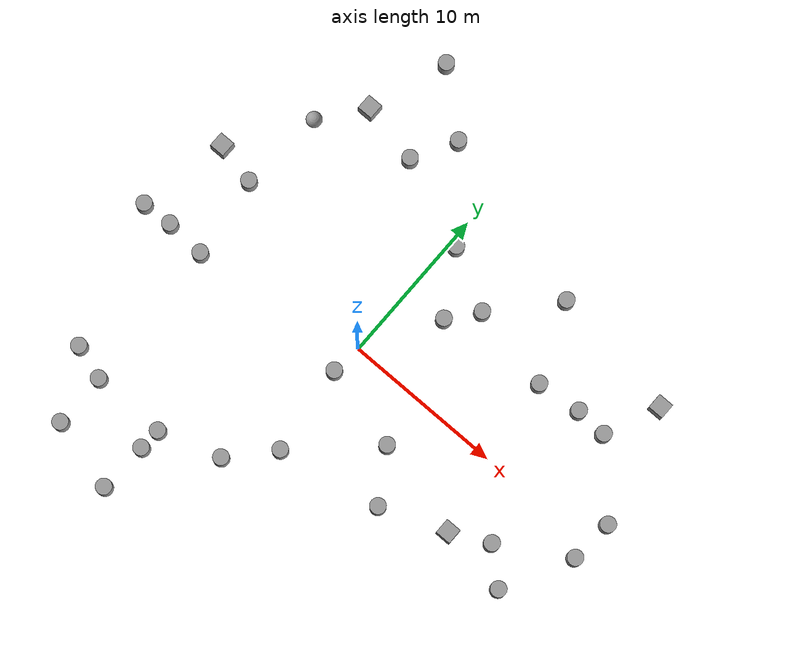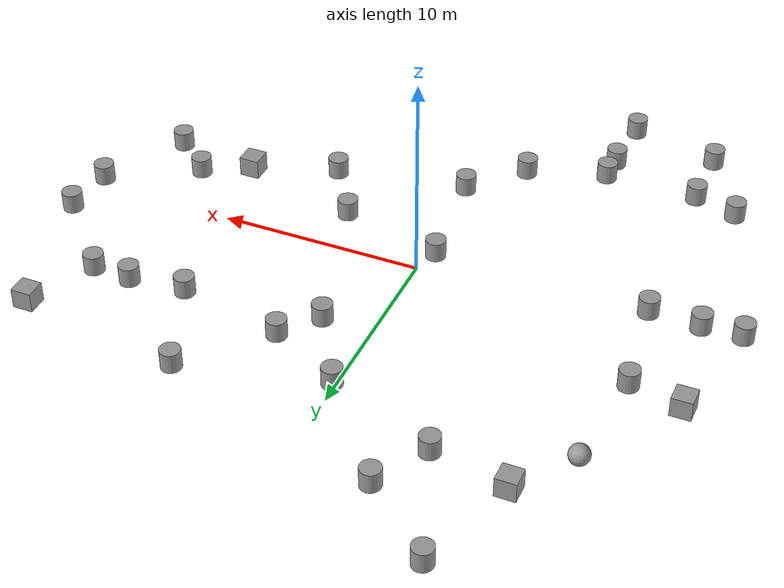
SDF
<?xml version='1.0'?>
<sdf version='1.7'>
  <model name='objetracetrack'>
    <link name='link_0'>
      <inertial>
        <mass>1</mass>
        <inertia>
          <ixx>0.145833</ixx>
          <ixy>0</ixy>
          <ixz>0</ixz>
          <iyy>0.145833</iyy>
          <iyz>0</iyz>
          <izz>0.125</izz>
        </inertia>
      </inertial>
      <pose>5.01054 -3.20804 0 0 -0 0</pose>
      <visual name='visual'>
        <pose>0 0 0 0 -0 0</pose>
        <geometry>
          <cylinder>
            <radius>0.5</radius>
            <length>1</length>
          </cylinder>
        </geometry>
        <material>
          <lighting>1</lighting>
          <script>
            <uri>file://media/materials/scripts/gazebo.material</uri>
            <name>Gazebo/Grey</name>
          </script>
          <shader type='pixel'/>
        </material>
        <transparency>0</transparency>
        <cast_shadows>1</cast_shadows>
      </visual>
      <collision name='collision'>
        <laser_retro>0</laser_retro>
        <max_contacts>10</max_contacts>
        <pose>0 0 0 0 -0 0</pose>
        <geometry>
          <cylinder>
            <radius>0.5</radius>
            <length>1</length>
          </cylinder>
        </geometry>
        <surface>
          <friction>
            <ode>
              <mu>1</mu>
              <mu2>1</mu2>
              <fdir1>0 0 0</fdir1>
              <slip1>0</slip1>
              <slip2>0</slip2>
            </ode>
            <torsional>
              <coefficient>1</coefficient>
              <patch_radius>0</patch_radius>
              <surface_radius>0</surface_radius>
              <use_patch_radius>1</use_patch_radius>
              <ode>
                <slip>0</slip>
              </ode>
            </torsional>
          </friction>
          <bounce>
            <restitution_coefficient>0</restitution_coefficient>
            <threshold>1e+06</threshold>
          </bounce>
          <contact>
            <collide_without_contact>0</collide_without_contact>
            <collide_without_contact_bitmask>1</collide_without_contact_bitmask>
            <collide_bitmask>1</collide_bitmask>
            <ode>
              <soft_cfm>0</soft_cfm>
              <soft_erp>0.2</soft_erp>
              <kp>1e+13</kp>
              <kd>1</kd>
              <max_vel>0.01</max_vel>
              <min_depth>0</min_depth>
            </ode>
            <bullet>
              <split_impulse>1</split_impulse>
              <split_impulse_penetration_threshold>-0.01</split_impulse_penetration_threshold>
              <soft_cfm>0</soft_cfm>
              <soft_erp>0.2</soft_erp>
              <kp>1e+13</kp>
              <kd>1</kd>
            </bullet>
          </contact>
        </surface>
      </collision>
    </link>
    <link name='link_1'>
      <inertial>
        <mass>1</mass>
        <inertia>
          <ixx>0.145833</ixx>
          <ixy>0</ixy>
          <ixz>0</ixz>
          <iyy>0.145833</iyy>
          <iyz>0</iyz>
          <izz>0.125</izz>
        </inertia>
      </inertial>
      <pose>6.93797 -6.26956 0 0 -0 0</pose>
      <visual name='visual'>
        <pose>0 0 0 0 -0 0</pose>
        <geometry>
          <cylinder>
            <radius>0.5</radius>
            <length>1</length>
          </cylinder>
        </geometry>
        <material>
          <lighting>1</lighting>
          <script>
            <uri>file://media/materials/scripts/gazebo.material</uri>
            <name>Gazebo/Grey</name>
          </script>
          <shader type='pixel'/>
        </material>
        <transparency>0</transparency>
        <cast_shadows>1</cast_shadows>
      </visual>
      <collision name='collision'>
        <laser_retro>0</laser_retro>
        <max_contacts>10</max_contacts>
        <pose>0 0 0 0 -0 0</pose>
        <geometry>
          <cylinder>
            <radius>0.5</radius>
            <length>1</length>
          </cylinder>
        </geometry>
        <surface>
          <friction>
            <ode>
              <mu>1</mu>
              <mu2>1</mu2>
              <fdir1>0 0 0</fdir1>
              <slip1>0</slip1>
              <slip2>0</slip2>
            </ode>
            <torsional>
              <coefficient>1</coefficient>
              <patch_radius>0</patch_radius>
              <surface_radius>0</surface_radius>
              <use_patch_radius>1</use_patch_radius>
              <ode>
                <slip>0</slip>
              </ode>
            </torsional>
          </friction>
          <bounce>
            <restitution_coefficient>0</restitution_coefficient>
            <threshold>1e+06</threshold>
          </bounce>
          <contact>
            <collide_without_contact>0</collide_without_contact>
            <collide_without_contact_bitmask>1</collide_without_contact_bitmask>
            <collide_bitmask>1</collide_bitmask>
            <ode>
              <soft_cfm>0</soft_cfm>
              <soft_erp>0.2</soft_erp>
              <kp>1e+13</kp>
              <kd>1</kd>
              <max_vel>0.01</max_vel>
              <min_depth>0</min_depth>
            </ode>
            <bullet>
              <split_impulse>1</split_impulse>
              <split_impulse_penetration_threshold>-0.01</split_impulse_penetration_threshold>
              <soft_cfm>0</soft_cfm>
              <soft_erp>0.2</soft_erp>
              <kp>1e+13</kp>
              <kd>1</kd>
            </bullet>
          </contact>
        </surface>
      </collision>
    </link>
    <link name='link_10'>
      <inertial>
        <mass>1</mass>
        <inertia>
          <ixx>0.145833</ixx>
          <ixy>0</ixy>
          <ixz>0</ixz>
          <iyy>0.145833</iyy>
          <iyz>0</iyz>
          <izz>0.125</izz>
        </inertia>
      </inertial>
      <pose>14.1744 5.54812 0 0 -0 0</pose>
      <visual name='visual'>
        <pose>0 0 0 0 -0 0</pose>
        <geometry>
          <cylinder>
            <radius>0.5</radius>
            <length>1</length>
          </cylinder>
        </geometry>
        <material>
          <lighting>1</lighting>
          <script>
            <uri>file://media/materials/scripts/gazebo.material</uri>
            <name>Gazebo/Grey</name>
          </script>
          <shader type='pixel'/>
        </material>
        <transparency>0</transparency>
        <cast_shadows>1</cast_shadows>
      </visual>
      <collision name='collision'>
        <laser_retro>0</laser_retro>
        <max_contacts>10</max_contacts>
        <pose>0 0 0 0 -0 0</pose>
        <geometry>
          <cylinder>
            <radius>0.5</radius>
            <length>1</length>
          </cylinder>
        </geometry>
        <surface>
          <friction>
            <ode>
              <mu>1</mu>
              <mu2>1</mu2>
              <fdir1>0 0 0</fdir1>
              <slip1>0</slip1>
              <slip2>0</slip2>
            </ode>
            <torsional>
              <coefficient>1</coefficient>
              <patch_radius>0</patch_radius>
              <surface_radius>0</surface_radius>
              <use_patch_radius>1</use_patch_radius>
              <ode>
                <slip>0</slip>
              </ode>
            </torsional>
          </friction>
          <bounce>
            <restitution_coefficient>0</restitution_coefficient>
            <threshold>1e+06</threshold>
          </bounce>
          <contact>
            <collide_without_contact>0</collide_without_contact>
            <collide_without_contact_bitmask>1</collide_without_contact_bitmask>
            <collide_bitmask>1</collide_bitmask>
            <ode>
              <soft_cfm>0</soft_cfm>
              <soft_erp>0.2</soft_erp>
              <kp>1e+13</kp>
              <kd>1</kd>
              <max_vel>0.01</max_vel>
              <min_depth>0</min_depth>
            </ode>
            <bullet>
              <split_impulse>1</split_impulse>
              <split_impulse_penetration_threshold>-0.01</split_impulse_penetration_threshold>
              <soft_cfm>0</soft_cfm>
              <soft_erp>0.2</soft_erp>
              <kp>1e+13</kp>
              <kd>1</kd>
            </bullet>
          </contact>
        </surface>
      </collision>
    </link>
    <link name='link_11'>
      <inertial>
        <mass>1</mass>
        <inertia>
          <ixx>0.166667</ixx>
          <ixy>0</ixy>
          <ixz>0</ixz>
          <iyy>0.166667</iyy>
          <iyz>0</iyz>
          <izz>0.166667</izz>
        </inertia>
      </inertial>
      <pose>15.6652 8.94561 0 0 -0 0</pose>
      <visual name='visual'>
        <pose>0 0 0 0 -0 0</pose>
        <geometry>
          <box>
            <size>1 1 1</size>
          </box>
        </geometry>
        <material>
          <lighting>1</lighting>
          <script>
            <uri>file://media/materials/scripts/gazebo.material</uri>
            <name>Gazebo/Grey</name>
          </script>
          <shader type='pixel'/>
        </material>
        <transparency>0</transparency>
        <cast_shadows>1</cast_shadows>
      </visual>
      <collision name='collision'>
        <laser_retro>0</laser_retro>
        <max_contacts>10</max_contacts>
        <pose>0 0 0 0 -0 0</pose>
        <geometry>
          <box>
            <size>1 1 1</size>
          </box>
        </geometry>
        <surface>
          <friction>
            <ode>
              <mu>1</mu>
              <mu2>1</mu2>
              <fdir1>0 0 0</fdir1>
              <slip1>0</slip1>
              <slip2>0</slip2>
            </ode>
            <torsional>
              <coefficient>1</coefficient>
              <patch_radius>0</patch_radius>
              <surface_radius>0</surface_radius>
              <use_patch_radius>1</use_patch_radius>
              <ode>
                <slip>0</slip>
              </ode>
            </torsional>
          </friction>
          <bounce>
            <restitution_coefficient>0</restitution_coefficient>
            <threshold>1e+06</threshold>
          </bounce>
          <contact>
            <collide_without_contact>0</collide_without_contact>
            <collide_without_contact_bitmask>1</collide_without_contact_bitmask>
            <collide_bitmask>1</collide_bitmask>
            <ode>
              <soft_cfm>0</soft_cfm>
              <soft_erp>0.2</soft_erp>
              <kp>1e+13</kp>
              <kd>1</kd>
              <max_vel>0.01</max_vel>
              <min_depth>0</min_depth>
            </ode>
            <bullet>
              <split_impulse>1</split_impulse>
              <split_impulse_penetration_threshold>-0.01</split_impulse_penetration_threshold>
              <soft_cfm>0</soft_cfm>
              <soft_erp>0.2</soft_erp>
              <kp>1e+13</kp>
              <kd>1</kd>
            </bullet>
          </contact>
        </surface>
      </collision>
    </link>
    <link name='link_12'>
      <inertial>
        <mass>1</mass>
        <inertia>
          <ixx>0.145833</ixx>
          <ixy>0</ixy>
          <ixz>0</ixz>
          <iyy>0.145833</iyy>
          <iyz>0</iyz>
          <izz>0.125</izz>
        </inertia>
      </inertial>
      <pose>7.44329 10.1909 0 0 -0 0</pose>
      <visual name='visual'>
        <pose>0 0 0 0 -0 0</pose>
        <geometry>
          <cylinder>
            <radius>0.5</radius>
            <length>1</length>
          </cylinder>
        </geometry>
        <material>
          <lighting>1</lighting>
          <script>
            <uri>file://media/materials/scripts/gazebo.material</uri>
            <name>Gazebo/Grey</name>
          </script>
          <shader type='pixel'/>
        </material>
        <transparency>0</transparency>
        <cast_shadows>1</cast_shadows>
      </visual>
      <collision name='collision'>
        <laser_retro>0</laser_retro>
        <max_contacts>10</max_contacts>
        <pose>0 0 0 0 -0 0</pose>
        <geometry>
          <cylinder>
            <radius>0.5</radius>
            <length>1</length>
          </cylinder>
        </geometry>
        <surface>
          <friction>
            <ode>
              <mu>1</mu>
              <mu2>1</mu2>
              <fdir1>0 0 0</fdir1>
              <slip1>0</slip1>
              <slip2>0</slip2>
            </ode>
            <torsional>
              <coefficient>1</coefficient>
              <patch_radius>0</patch_radius>
              <surface_radius>0</surface_radius>
              <use_patch_radius>1</use_patch_radius>
              <ode>
                <slip>0</slip>
              </ode>
            </torsional>
          </friction>
          <bounce>
            <restitution_coefficient>0</restitution_coefficient>
            <threshold>1e+06</threshold>
          </bounce>
          <contact>
            <collide_without_contact>0</collide_without_contact>
            <collide_without_contact_bitmask>1</collide_without_contact_bitmask>
            <collide_bitmask>1</collide_bitmask>
            <ode>
              <soft_cfm>0</soft_cfm>
              <soft_erp>0.2</soft_erp>
              <kp>1e+13</kp>
              <kd>1</kd>
              <max_vel>0.01</max_vel>
              <min_depth>0</min_depth>
            </ode>
            <bullet>
              <split_impulse>1</split_impulse>
              <split_impulse_penetration_threshold>-0.01</split_impulse_penetration_threshold>
              <soft_cfm>0</soft_cfm>
              <soft_erp>0.2</soft_erp>
              <kp>1e+13</kp>
              <kd>1</kd>
            </bullet>
          </contact>
        </surface>
      </collision>
    </link>
    <link name='link_13'>
      <inertial>
        <mass>1</mass>
        <inertia>
          <ixx>0.145833</ixx>
          <ixy>0</ixy>
          <ixz>0</ixz>
          <iyy>0.145833</iyy>
          <iyz>0</iyz>
          <izz>0.125</izz>
        </inertia>
      </inertial>
      <pose>9.41915 5.35781 0 0 -0 0</pose>
      <visual name='visual'>
        <pose>0 0 0 0 -0 0</pose>
        <geometry>
          <cylinder>
            <radius>0.5</radius>
            <length>1</length>
          </cylinder>
        </geometry>
        <material>
          <lighting>1</lighting>
          <script>
            <uri>file://media/materials/scripts/gazebo.material</uri>
            <name>Gazebo/Grey</name>
          </script>
          <shader type='pixel'/>
        </material>
        <transparency>0</transparency>
        <cast_shadows>1</cast_shadows>
      </visual>
      <collision name='collision'>
        <laser_retro>0</laser_retro>
        <max_contacts>10</max_contacts>
        <pose>0 0 0 0 -0 0</pose>
        <geometry>
          <cylinder>
            <radius>0.5</radius>
            <length>1</length>
          </cylinder>
        </geometry>
        <surface>
          <friction>
            <ode>
              <mu>1</mu>
              <mu2>1</mu2>
              <fdir1>0 0 0</fdir1>
              <slip1>0</slip1>
              <slip2>0</slip2>
            </ode>
            <torsional>
              <coefficient>1</coefficient>
              <patch_radius>0</patch_radius>
              <surface_radius>0</surface_radius>
              <use_patch_radius>1</use_patch_radius>
              <ode>
                <slip>0</slip>
              </ode>
            </torsional>
          </friction>
          <bounce>
            <restitution_coefficient>0</restitution_coefficient>
            <threshold>1e+06</threshold>
          </bounce>
          <contact>
            <collide_without_contact>0</collide_without_contact>
            <collide_without_contact_bitmask>1</collide_without_contact_bitmask>
            <collide_bitmask>1</collide_bitmask>
            <ode>
              <soft_cfm>0</soft_cfm>
              <soft_erp>0.2</soft_erp>
              <kp>1e+13</kp>
              <kd>1</kd>
              <max_vel>0.01</max_vel>
              <min_depth>0</min_depth>
            </ode>
            <bullet>
              <split_impulse>1</split_impulse>
              <split_impulse_penetration_threshold>-0.01</split_impulse_penetration_threshold>
              <soft_cfm>0</soft_cfm>
              <soft_erp>0.2</soft_erp>
              <kp>1e+13</kp>
              <kd>1</kd>
            </bullet>
          </contact>
        </surface>
      </collision>
    </link>
    <link name='link_14'>
      <inertial>
        <mass>1</mass>
        <inertia>
          <ixx>0.145833</ixx>
          <ixy>0</ixy>
          <ixz>0</ixz>
          <iyy>0.145833</iyy>
          <iyz>0</iyz>
          <izz>0.125</izz>
        </inertia>
      </inertial>
      <pose>4.1131 6.43948 0 0 -0 0</pose>
      <visual name='visual'>
        <pose>0 0 0 0 -0 0</pose>
        <geometry>
          <cylinder>
            <radius>0.5</radius>
            <length>1</length>
          </cylinder>
        </geometry>
        <material>
          <lighting>1</lighting>
          <script>
            <uri>file://media/materials/scripts/gazebo.material</uri>
            <name>Gazebo/Grey</name>
          </script>
          <shader type='pixel'/>
        </material>
        <transparency>0</transparency>
        <cast_shadows>1</cast_shadows>
      </visual>
      <collision name='collision'>
        <laser_retro>0</laser_retro>
        <max_contacts>10</max_contacts>
        <pose>0 0 0 0 -0 0</pose>
        <geometry>
          <cylinder>
            <radius>0.5</radius>
            <length>1</length>
          </cylinder>
        </geometry>
        <surface>
          <friction>
            <ode>
              <mu>1</mu>
              <mu2>1</mu2>
              <fdir1>0 0 0</fdir1>
              <slip1>0</slip1>
              <slip2>0</slip2>
            </ode>
            <torsional>
              <coefficient>1</coefficient>
              <patch_radius>0</patch_radius>
              <surface_radius>0</surface_radius>
              <use_patch_radius>1</use_patch_radius>
              <ode>
                <slip>0</slip>
              </ode>
            </torsional>
          </friction>
          <bounce>
            <restitution_coefficient>0</restitution_coefficient>
            <threshold>1e+06</threshold>
          </bounce>
          <contact>
            <collide_without_contact>0</collide_without_contact>
            <collide_without_contact_bitmask>1</collide_without_contact_bitmask>
            <collide_bitmask>1</collide_bitmask>
            <ode>
              <soft_cfm>0</soft_cfm>
              <soft_erp>0.2</soft_erp>
              <kp>1e+13</kp>
              <kd>1</kd>
              <max_vel>0.01</max_vel>
              <min_depth>0</min_depth>
            </ode>
            <bullet>
              <split_impulse>1</split_impulse>
              <split_impulse_penetration_threshold>-0.01</split_impulse_penetration_threshold>
              <soft_cfm>0</soft_cfm>
              <soft_erp>0.2</soft_erp>
              <kp>1e+13</kp>
              <kd>1</kd>
            </bullet>
          </contact>
        </surface>
      </collision>
    </link>
    <link name='link_15'>
      <inertial>
        <mass>1</mass>
        <inertia>
          <ixx>0.145833</ixx>
          <ixy>0</ixy>
          <ixz>0</ixz>
          <iyy>0.145833</iyy>
          <iyz>0</iyz>
          <izz>0.125</izz>
        </inertia>
      </inertial>
      <pose>2.67704 4.64369 0 0 -0 0</pose>
      <visual name='visual'>
        <pose>0 0 0 0 -0 0</pose>
        <geometry>
          <cylinder>
            <radius>0.5</radius>
            <length>1</length>
          </cylinder>
        </geometry>
        <material>
          <lighting>1</lighting>
          <script>
            <uri>file://media/materials/scripts/gazebo.material</uri>
            <name>Gazebo/Grey</name>
          </script>
          <shader type='pixel'/>
        </material>
        <transparency>0</transparency>
        <cast_shadows>1</cast_shadows>
      </visual>
      <collision name='collision'>
        <laser_retro>0</laser_retro>
        <max_contacts>10</max_contacts>
        <pose>0 0 0 0 -0 0</pose>
        <geometry>
          <cylinder>
            <radius>0.5</radius>
            <length>1</length>
          </cylinder>
        </geometry>
        <surface>
          <friction>
            <ode>
              <mu>1</mu>
              <mu2>1</mu2>
              <fdir1>0 0 0</fdir1>
              <slip1>0</slip1>
              <slip2>0</slip2>
            </ode>
            <torsional>
              <coefficient>1</coefficient>
              <patch_radius>0</patch_radius>
              <surface_radius>0</surface_radius>
              <use_patch_radius>1</use_patch_radius>
              <ode>
                <slip>0</slip>
              </ode>
            </torsional>
          </friction>
          <bounce>
            <restitution_coefficient>0</restitution_coefficient>
            <threshold>1e+06</threshold>
          </bounce>
          <contact>
            <collide_without_contact>0</collide_without_contact>
            <collide_without_contact_bitmask>1</collide_without_contact_bitmask>
            <collide_bitmask>1</collide_bitmask>
            <ode>
              <soft_cfm>0</soft_cfm>
              <soft_erp>0.2</soft_erp>
              <kp>1e+13</kp>
              <kd>1</kd>
              <max_vel>0.01</max_vel>
              <min_depth>0</min_depth>
            </ode>
            <bullet>
              <split_impulse>1</split_impulse>
              <split_impulse_penetration_threshold>-0.01</split_impulse_penetration_threshold>
              <soft_cfm>0</soft_cfm>
              <soft_erp>0.2</soft_erp>
              <kp>1e+13</kp>
              <kd>1</kd>
            </bullet>
          </contact>
        </surface>
      </collision>
    </link>
    <link name='link_16'>
      <inertial>
        <mass>1</mass>
        <inertia>
          <ixx>0.145833</ixx>
          <ixy>0</ixy>
          <ixz>0</ixz>
          <iyy>0.145833</iyy>
          <iyz>0</iyz>
          <izz>0.125</izz>
        </inertia>
      </inertial>
      <pose>0.43334 8.40793 0 0 -0 0</pose>
      <visual name='visual'>
        <pose>0 0 0 0 -0 0</pose>
        <geometry>
          <cylinder>
            <radius>0.5</radius>
            <length>1</length>
          </cylinder>
        </geometry>
        <material>
          <lighting>1</lighting>
          <script>
            <uri>file://media/materials/scripts/gazebo.material</uri>
            <name>Gazebo/Grey</name>
          </script>
          <shader type='pixel'/>
        </material>
        <transparency>0</transparency>
        <cast_shadows>1</cast_shadows>
      </visual>
      <collision name='collision'>
        <laser_retro>0</laser_retro>
        <max_contacts>10</max_contacts>
        <pose>0 0 0 0 -0 0</pose>
        <geometry>
          <cylinder>
            <radius>0.5</radius>
            <length>1</length>
          </cylinder>
        </geometry>
        <surface>
          <friction>
            <ode>
              <mu>1</mu>
              <mu2>1</mu2>
              <fdir1>0 0 0</fdir1>
              <slip1>0</slip1>
              <slip2>0</slip2>
            </ode>
            <torsional>
              <coefficient>1</coefficient>
              <patch_radius>0</patch_radius>
              <surface_radius>0</surface_radius>
              <use_patch_radius>1</use_patch_radius>
              <ode>
                <slip>0</slip>
              </ode>
            </torsional>
          </friction>
          <bounce>
            <restitution_coefficient>0</restitution_coefficient>
            <threshold>1e+06</threshold>
          </bounce>
          <contact>
            <collide_without_contact>0</collide_without_contact>
            <collide_without_contact_bitmask>1</collide_without_contact_bitmask>
            <collide_bitmask>1</collide_bitmask>
            <ode>
              <soft_cfm>0</soft_cfm>
              <soft_erp>0.2</soft_erp>
              <kp>1e+13</kp>
              <kd>1</kd>
              <max_vel>0.01</max_vel>
              <min_depth>0</min_depth>
            </ode>
            <bullet>
              <split_impulse>1</split_impulse>
              <split_impulse_penetration_threshold>-0.01</split_impulse_penetration_threshold>
              <soft_cfm>0</soft_cfm>
              <soft_erp>0.2</soft_erp>
              <kp>1e+13</kp>
              <kd>1</kd>
            </bullet>
          </contact>
        </surface>
      </collision>
    </link>
    <link name='link_17'>
      <inertial>
        <mass>1</mass>
        <inertia>
          <ixx>0.145833</ixx>
          <ixy>0</ixy>
          <ixz>0</ixz>
          <iyy>0.145833</iyy>
          <iyz>0</iyz>
          <izz>0.125</izz>
        </inertia>
      </inertial>
      <pose>-5.12652 10.6879 0 0 -0 0</pose>
      <visual name='visual'>
        <pose>0 0 0 0 -0 0</pose>
        <geometry>
          <cylinder>
            <radius>0.5</radius>
            <length>1</length>
          </cylinder>
        </geometry>
        <material>
          <lighting>1</lighting>
          <script>
            <uri>file://media/materials/scripts/gazebo.material</uri>
            <name>Gazebo/Grey</name>
          </script>
          <shader type='pixel'/>
        </material>
        <transparency>0</transparency>
        <cast_shadows>1</cast_shadows>
      </visual>
      <collision name='collision'>
        <laser_retro>0</laser_retro>
        <max_contacts>10</max_contacts>
        <pose>0 0 0 0 -0 0</pose>
        <geometry>
          <cylinder>
            <radius>0.5</radius>
            <length>1</length>
          </cylinder>
        </geometry>
        <surface>
          <friction>
            <ode>
              <mu>1</mu>
              <mu2>1</mu2>
              <fdir1>0 0 0</fdir1>
              <slip1>0</slip1>
              <slip2>0</slip2>
            </ode>
            <torsional>
              <coefficient>1</coefficient>
              <patch_radius>0</patch_radius>
              <surface_radius>0</surface_radius>
              <use_patch_radius>1</use_patch_radius>
              <ode>
                <slip>0</slip>
              </ode>
            </torsional>
          </friction>
          <bounce>
            <restitution_coefficient>0</restitution_coefficient>
            <threshold>1e+06</threshold>
          </bounce>
          <contact>
            <collide_without_contact>0</collide_without_contact>
            <collide_without_contact_bitmask>1</collide_without_contact_bitmask>
            <collide_bitmask>1</collide_bitmask>
            <ode>
              <soft_cfm>0</soft_cfm>
              <soft_erp>0.2</soft_erp>
              <kp>1e+13</kp>
              <kd>1</kd>
              <max_vel>0.01</max_vel>
              <min_depth>0</min_depth>
            </ode>
            <bullet>
              <split_impulse>1</split_impulse>
              <split_impulse_penetration_threshold>-0.01</split_impulse_penetration_threshold>
              <soft_cfm>0</soft_cfm>
              <soft_erp>0.2</soft_erp>
              <kp>1e+13</kp>
              <kd>1</kd>
            </bullet>
          </contact>
        </surface>
      </collision>
    </link>
    <link name='link_18'>
      <inertial>
        <mass>1</mass>
        <inertia>
          <ixx>0.145833</ixx>
          <ixy>0</ixy>
          <ixz>0</ixz>
          <iyy>0.145833</iyy>
          <iyz>0</iyz>
          <izz>0.125</izz>
        </inertia>
      </inertial>
      <pose>-3.63413 13.3905 0 0 -0 0</pose>
      <visual name='visual'>
        <pose>0 0 0 0 -0 0</pose>
        <geometry>
          <cylinder>
            <radius>0.5</radius>
            <length>1</length>
          </cylinder>
        </geometry>
        <material>
          <lighting>1</lighting>
          <script>
            <uri>file://media/materials/scripts/gazebo.material</uri>
            <name>Gazebo/Grey</name>
          </script>
          <shader type='pixel'/>
        </material>
        <transparency>0</transparency>
        <cast_shadows>1</cast_shadows>
      </visual>
      <collision name='collision'>
        <laser_retro>0</laser_retro>
        <max_contacts>10</max_contacts>
        <pose>0 0 0 0 -0 0</pose>
        <geometry>
          <cylinder>
            <radius>0.5</radius>
            <length>1</length>
          </cylinder>
        </geometry>
        <surface>
          <friction>
            <ode>
              <mu>1</mu>
              <mu2>1</mu2>
              <fdir1>0 0 0</fdir1>
              <slip1>0</slip1>
              <slip2>0</slip2>
            </ode>
            <torsional>
              <coefficient>1</coefficient>
              <patch_radius>0</patch_radius>
              <surface_radius>0</surface_radius>
              <use_patch_radius>1</use_patch_radius>
              <ode>
                <slip>0</slip>
              </ode>
            </torsional>
          </friction>
          <bounce>
            <restitution_coefficient>0</restitution_coefficient>
            <threshold>1e+06</threshold>
          </bounce>
          <contact>
            <collide_without_contact>0</collide_without_contact>
            <collide_without_contact_bitmask>1</collide_without_contact_bitmask>
            <collide_bitmask>1</collide_bitmask>
            <ode>
              <soft_cfm>0</soft_cfm>
              <soft_erp>0.2</soft_erp>
              <kp>1e+13</kp>
              <kd>1</kd>
              <max_vel>0.01</max_vel>
              <min_depth>0</min_depth>
            </ode>
            <bullet>
              <split_impulse>1</split_impulse>
              <split_impulse_penetration_threshold>-0.01</split_impulse_penetration_threshold>
              <soft_cfm>0</soft_cfm>
              <soft_erp>0.2</soft_erp>
              <kp>1e+13</kp>
              <kd>1</kd>
            </bullet>
          </contact>
        </surface>
      </collision>
    </link>
    <link name='link_19'>
      <inertial>
        <mass>1</mass>
        <inertia>
          <ixx>0.145833</ixx>
          <ixy>0</ixy>
          <ixz>0</ixz>
          <iyy>0.145833</iyy>
          <iyz>0</iyz>
          <izz>0.125</izz>
        </inertia>
      </inertial>
      <pose>-7.25312 16.5161 0 0 -0 0</pose>
      <visual name='visual'>
        <pose>0 0 0 0 -0 0</pose>
        <geometry>
          <cylinder>
            <radius>0.5</radius>
            <length>1</length>
          </cylinder>
        </geometry>
        <material>
          <lighting>1</lighting>
          <script>
            <uri>file://media/materials/scripts/gazebo.material</uri>
            <name>Gazebo/Grey</name>
          </script>
          <shader type='pixel'/>
        </material>
        <transparency>0</transparency>
        <cast_shadows>1</cast_shadows>
      </visual>
      <collision name='collision'>
        <laser_retro>0</laser_retro>
        <max_contacts>10</max_contacts>
        <pose>0 0 0 0 -0 0</pose>
        <geometry>
          <cylinder>
            <radius>0.5</radius>
            <length>1</length>
          </cylinder>
        </geometry>
        <surface>
          <friction>
            <ode>
              <mu>1</mu>
              <mu2>1</mu2>
              <fdir1>0 0 0</fdir1>
              <slip1>0</slip1>
              <slip2>0</slip2>
            </ode>
            <torsional>
              <coefficient>1</coefficient>
              <patch_radius>0</patch_radius>
              <surface_radius>0</surface_radius>
              <use_patch_radius>1</use_patch_radius>
              <ode>
                <slip>0</slip>
              </ode>
            </torsional>
          </friction>
          <bounce>
            <restitution_coefficient>0</restitution_coefficient>
            <threshold>1e+06</threshold>
          </bounce>
          <contact>
            <collide_without_contact>0</collide_without_contact>
            <collide_without_contact_bitmask>1</collide_without_contact_bitmask>
            <collide_bitmask>1</collide_bitmask>
            <ode>
              <soft_cfm>0</soft_cfm>
              <soft_erp>0.2</soft_erp>
              <kp>1e+13</kp>
              <kd>1</kd>
              <max_vel>0.01</max_vel>
              <min_depth>0</min_depth>
            </ode>
            <bullet>
              <split_impulse>1</split_impulse>
              <split_impulse_penetration_threshold>-0.01</split_impulse_penetration_threshold>
              <soft_cfm>0</soft_cfm>
              <soft_erp>0.2</soft_erp>
              <kp>1e+13</kp>
              <kd>1</kd>
            </bullet>
          </contact>
        </surface>
      </collision>
    </link>
    <link name='link_20'>
      <inertial>
        <mass>1</mass>
        <inertia>
          <ixx>0.166667</ixx>
          <ixy>0</ixy>
          <ixz>0</ixz>
          <iyy>0.166667</iyy>
          <iyz>0</iyz>
          <izz>0.166667</izz>
        </inertia>
      </inertial>
      <pose>-8.94757 11.4807 0 0 -0 0</pose>
      <visual name='visual'>
        <pose>0 0 0 0 -0 0</pose>
        <geometry>
          <box>
            <size>1 1 1</size>
          </box>
        </geometry>
        <material>
          <lighting>1</lighting>
          <script>
            <uri>file://media/materials/scripts/gazebo.material</uri>
            <name>Gazebo/Grey</name>
          </script>
          <shader type='pixel'/>
        </material>
        <transparency>0</transparency>
        <cast_shadows>1</cast_shadows>
      </visual>
      <collision name='collision'>
        <laser_retro>0</laser_retro>
        <max_contacts>10</max_contacts>
        <pose>0 0 0 0 -0 0</pose>
        <geometry>
          <box>
            <size>1 1 1</size>
          </box>
        </geometry>
        <surface>
          <friction>
            <ode>
              <mu>1</mu>
              <mu2>1</mu2>
              <fdir1>0 0 0</fdir1>
              <slip1>0</slip1>
              <slip2>0</slip2>
            </ode>
            <torsional>
              <coefficient>1</coefficient>
              <patch_radius>0</patch_radius>
              <surface_radius>0</surface_radius>
              <use_patch_radius>1</use_patch_radius>
              <ode>
                <slip>0</slip>
              </ode>
            </torsional>
          </friction>
          <bounce>
            <restitution_coefficient>0</restitution_coefficient>
            <threshold>1e+06</threshold>
          </bounce>
          <contact>
            <collide_without_contact>0</collide_without_contact>
            <collide_without_contact_bitmask>1</collide_without_contact_bitmask>
            <collide_bitmask>1</collide_bitmask>
            <ode>
              <soft_cfm>0</soft_cfm>
              <soft_erp>0.2</soft_erp>
              <kp>1e+13</kp>
              <kd>1</kd>
              <max_vel>0.01</max_vel>
              <min_depth>0</min_depth>
            </ode>
            <bullet>
              <split_impulse>1</split_impulse>
              <split_impulse_penetration_threshold>-0.01</split_impulse_penetration_threshold>
              <soft_cfm>0</soft_cfm>
              <soft_erp>0.2</soft_erp>
              <kp>1e+13</kp>
              <kd>1</kd>
            </bullet>
          </contact>
        </surface>
      </collision>
    </link>
    <link name='link_21'>
      <inertial>
        <mass>1</mass>
        <inertia>
          <ixx>0.1</ixx>
          <ixy>0</ixy>
          <ixz>0</ixz>
          <iyy>0.1</iyy>
          <iyz>0</iyz>
          <izz>0.1</izz>
        </inertia>
      </inertial>
      <pose>-11.037 8.79509 0 0 -0 0</pose>
      <visual name='visual'>
        <pose>0 0 0 0 -0 0</pose>
        <geometry>
          <sphere>
            <radius>0.5</radius>
          </sphere>
        </geometry>
        <material>
          <lighting>1</lighting>
          <script>
            <uri>file://media/materials/scripts/gazebo.material</uri>
            <name>Gazebo/Grey</name>
          </script>
          <shader type='pixel'/>
        </material>
        <transparency>0</transparency>
        <cast_shadows>1</cast_shadows>
      </visual>
      <collision name='collision'>
        <laser_retro>0</laser_retro>
        <max_contacts>10</max_contacts>
        <pose>0 0 0 0 -0 0</pose>
        <geometry>
          <sphere>
            <radius>0.5</radius>
          </sphere>
        </geometry>
        <surface>
          <friction>
            <ode>
              <mu>1</mu>
              <mu2>1</mu2>
              <fdir1>0 0 0</fdir1>
              <slip1>0</slip1>
              <slip2>0</slip2>
            </ode>
            <torsional>
              <coefficient>1</coefficient>
              <patch_radius>0</patch_radius>
              <surface_radius>0</surface_radius>
              <use_patch_radius>1</use_patch_radius>
              <ode>
                <slip>0</slip>
              </ode>
            </torsional>
          </friction>
          <bounce>
            <restitution_coefficient>0</restitution_coefficient>
            <threshold>1e+06</threshold>
          </bounce>
          <contact>
            <collide_without_contact>0</collide_without_contact>
            <collide_without_contact_bitmask>1</collide_without_contact_bitmask>
            <collide_bitmask>1</collide_bitmask>
            <ode>
              <soft_cfm>0</soft_cfm>
              <soft_erp>0.2</soft_erp>
              <kp>1e+13</kp>
              <kd>1</kd>
              <max_vel>0.01</max_vel>
              <min_depth>0</min_depth>
            </ode>
            <bullet>
              <split_impulse>1</split_impulse>
              <split_impulse_penetration_threshold>-0.01</split_impulse_penetration_threshold>
              <soft_cfm>0</soft_cfm>
              <soft_erp>0.2</soft_erp>
              <kp>1e+13</kp>
              <kd>1</kd>
            </bullet>
          </contact>
        </surface>
      </collision>
    </link>
    <link name='link_22'>
      <inertial>
        <mass>1</mass>
        <inertia>
          <ixx>0.166667</ixx>
          <ixy>0</ixy>
          <ixz>0</ixz>
          <iyy>0.166667</iyy>
          <iyz>0</iyz>
          <izz>0.166667</izz>
        </inertia>
      </inertial>
      <pose>-14.1076 3.99625 0 0 -0 0</pose>
      <visual name='visual'>
        <pose>0 0 0 0 -0 0</pose>
        <geometry>
          <box>
            <size>1 1 1</size>
          </box>
        </geometry>
        <material>
          <lighting>1</lighting>
          <script>
            <uri>file://media/materials/scripts/gazebo.material</uri>
            <name>Gazebo/Grey</name>
          </script>
          <shader type='pixel'/>
        </material>
        <transparency>0</transparency>
        <cast_shadows>1</cast_shadows>
      </visual>
      <collision name='collision'>
        <laser_retro>0</laser_retro>
        <max_contacts>10</max_contacts>
        <pose>0 0 0 0 -0 0</pose>
        <geometry>
          <box>
            <size>1 1 1</size>
          </box>
        </geometry>
        <surface>
          <friction>
            <ode>
              <mu>1</mu>
              <mu2>1</mu2>
              <fdir1>0 0 0</fdir1>
              <slip1>0</slip1>
              <slip2>0</slip2>
            </ode>
            <torsional>
              <coefficient>1</coefficient>
              <patch_radius>0</patch_radius>
              <surface_radius>0</surface_radius>
              <use_patch_radius>1</use_patch_radius>
              <ode>
                <slip>0</slip>
              </ode>
            </torsional>
          </friction>
          <bounce>
            <restitution_coefficient>0</restitution_coefficient>
            <threshold>1e+06</threshold>
          </bounce>
          <contact>
            <collide_without_contact>0</collide_without_contact>
            <collide_without_contact_bitmask>1</collide_without_contact_bitmask>
            <collide_bitmask>1</collide_bitmask>
            <ode>
              <soft_cfm>0</soft_cfm>
              <soft_erp>0.2</soft_erp>
              <kp>1e+13</kp>
              <kd>1</kd>
              <max_vel>0.01</max_vel>
              <min_depth>0</min_depth>
            </ode>
            <bullet>
              <split_impulse>1</split_impulse>
              <split_impulse_penetration_threshold>-0.01</split_impulse_penetration_threshold>
              <soft_cfm>0</soft_cfm>
              <soft_erp>0.2</soft_erp>
              <kp>1e+13</kp>
              <kd>1</kd>
            </bullet>
          </contact>
        </surface>
      </collision>
    </link>
    <link name='link_23'>
      <inertial>
        <mass>1</mass>
        <inertia>
          <ixx>0.145833</ixx>
          <ixy>0</ixy>
          <ixz>0</ixz>
          <iyy>0.145833</iyy>
          <iyz>0</iyz>
          <izz>0.125</izz>
        </inertia>
      </inertial>
      <pose>-10.8016 -1.75228 0 0 -0 0</pose>
      <visual name='visual'>
        <pose>0 0 0 0 -0 0</pose>
        <geometry>
          <cylinder>
            <radius>0.5</radius>
            <length>1</length>
          </cylinder>
        </geometry>
        <material>
          <lighting>1</lighting>
          <script>
            <uri>file://media/materials/scripts/gazebo.material</uri>
            <name>Gazebo/Grey</name>
          </script>
          <shader type='pixel'/>
        </material>
        <transparency>0</transparency>
        <cast_shadows>1</cast_shadows>
      </visual>
      <collision name='collision'>
        <laser_retro>0</laser_retro>
        <max_contacts>10</max_contacts>
        <pose>0 0 0 0 -0 0</pose>
        <geometry>
          <cylinder>
            <radius>0.5</radius>
            <length>1</length>
          </cylinder>
        </geometry>
        <surface>
          <friction>
            <ode>
              <mu>1</mu>
              <mu2>1</mu2>
              <fdir1>0 0 0</fdir1>
              <slip1>0</slip1>
              <slip2>0</slip2>
            </ode>
            <torsional>
              <coefficient>1</coefficient>
              <patch_radius>0</patch_radius>
              <surface_radius>0</surface_radius>
              <use_patch_radius>1</use_patch_radius>
              <ode>
                <slip>0</slip>
              </ode>
            </torsional>
          </friction>
          <bounce>
            <restitution_coefficient>0</restitution_coefficient>
            <threshold>1e+06</threshold>
          </bounce>
          <contact>
            <collide_without_contact>0</collide_without_contact>
            <collide_without_contact_bitmask>1</collide_without_contact_bitmask>
            <collide_bitmask>1</collide_bitmask>
            <ode>
              <soft_cfm>0</soft_cfm>
              <soft_erp>0.2</soft_erp>
              <kp>1e+13</kp>
              <kd>1</kd>
              <max_vel>0.01</max_vel>
              <min_depth>0</min_depth>
            </ode>
            <bullet>
              <split_impulse>1</split_impulse>
              <split_impulse_penetration_threshold>-0.01</split_impulse_penetration_threshold>
              <soft_cfm>0</soft_cfm>
              <soft_erp>0.2</soft_erp>
              <kp>1e+13</kp>
              <kd>1</kd>
            </bullet>
          </contact>
        </surface>
      </collision>
    </link>
    <link name='link_24'>
      <inertial>
        <mass>1</mass>
        <inertia>
          <ixx>0.145833</ixx>
          <ixy>0</ixy>
          <ixz>0</ixz>
          <iyy>0.145833</iyy>
          <iyz>0</iyz>
          <izz>0.125</izz>
        </inertia>
      </inertial>
      <pose>-13.3144 -1.61028 0 0 -0 0</pose>
      <visual name='visual'>
        <pose>0 0 0 0 -0 0</pose>
        <geometry>
          <cylinder>
            <radius>0.5</radius>
            <length>1</length>
          </cylinder>
        </geometry>
        <material>
          <lighting>1</lighting>
          <script>
            <uri>file://media/materials/scripts/gazebo.material</uri>
            <name>Gazebo/Grey</name>
          </script>
          <shader type='pixel'/>
        </material>
        <transparency>0</transparency>
        <cast_shadows>1</cast_shadows>
      </visual>
      <collision name='collision'>
        <laser_retro>0</laser_retro>
        <max_contacts>10</max_contacts>
        <pose>0 0 0 0 -0 0</pose>
        <geometry>
          <cylinder>
            <radius>0.5</radius>
            <length>1</length>
          </cylinder>
        </geometry>
        <surface>
          <friction>
            <ode>
              <mu>1</mu>
              <mu2>1</mu2>
              <fdir1>0 0 0</fdir1>
              <slip1>0</slip1>
              <slip2>0</slip2>
            </ode>
            <torsional>
              <coefficient>1</coefficient>
              <patch_radius>0</patch_radius>
              <surface_radius>0</surface_radius>
              <use_patch_radius>1</use_patch_radius>
              <ode>
                <slip>0</slip>
              </ode>
            </torsional>
          </friction>
          <bounce>
            <restitution_coefficient>0</restitution_coefficient>
            <threshold>1e+06</threshold>
          </bounce>
          <contact>
            <collide_without_contact>0</collide_without_contact>
            <collide_without_contact_bitmask>1</collide_without_contact_bitmask>
            <collide_bitmask>1</collide_bitmask>
            <ode>
              <soft_cfm>0</soft_cfm>
              <soft_erp>0.2</soft_erp>
              <kp>1e+13</kp>
              <kd>1</kd>
              <max_vel>0.01</max_vel>
              <min_depth>0</min_depth>
            </ode>
            <bullet>
              <split_impulse>1</split_impulse>
              <split_impulse_penetration_threshold>-0.01</split_impulse_penetration_threshold>
              <soft_cfm>0</soft_cfm>
              <soft_erp>0.2</soft_erp>
              <kp>1e+13</kp>
              <kd>1</kd>
            </bullet>
          </contact>
        </surface>
      </collision>
    </link>
    <link name='link_25'>
      <inertial>
        <mass>1</mass>
        <inertia>
          <ixx>0.145833</ixx>
          <ixy>0</ixy>
          <ixz>0</ixz>
          <iyy>0.145833</iyy>
          <iyz>0</iyz>
          <izz>0.125</izz>
        </inertia>
      </inertial>
      <pose>-15.263 -1.6902 0 0 -0 0</pose>
      <visual name='visual'>
        <pose>0 0 0 0 -0 0</pose>
        <geometry>
          <cylinder>
            <radius>0.5</radius>
            <length>1</length>
          </cylinder>
        </geometry>
        <material>
          <lighting>1</lighting>
          <script>
            <uri>file://media/materials/scripts/gazebo.material</uri>
            <name>Gazebo/Grey</name>
          </script>
          <shader type='pixel'/>
        </material>
        <transparency>0</transparency>
        <cast_shadows>1</cast_shadows>
      </visual>
      <collision name='collision'>
        <laser_retro>0</laser_retro>
        <max_contacts>10</max_contacts>
        <pose>0 0 0 0 -0 0</pose>
        <geometry>
          <cylinder>
            <radius>0.5</radius>
            <length>1</length>
          </cylinder>
        </geometry>
        <surface>
          <friction>
            <ode>
              <mu>1</mu>
              <mu2>1</mu2>
              <fdir1>0 0 0</fdir1>
              <slip1>0</slip1>
              <slip2>0</slip2>
            </ode>
            <torsional>
              <coefficient>1</coefficient>
              <patch_radius>0</patch_radius>
              <surface_radius>0</surface_radius>
              <use_patch_radius>1</use_patch_radius>
              <ode>
                <slip>0</slip>
              </ode>
            </torsional>
          </friction>
          <bounce>
            <restitution_coefficient>0</restitution_coefficient>
            <threshold>1e+06</threshold>
          </bounce>
          <contact>
            <collide_without_contact>0</collide_without_contact>
            <collide_without_contact_bitmask>1</collide_without_contact_bitmask>
            <collide_bitmask>1</collide_bitmask>
            <ode>
              <soft_cfm>0</soft_cfm>
              <soft_erp>0.2</soft_erp>
              <kp>1e+13</kp>
              <kd>1</kd>
              <max_vel>0.01</max_vel>
              <min_depth>0</min_depth>
            </ode>
            <bullet>
              <split_impulse>1</split_impulse>
              <split_impulse_penetration_threshold>-0.01</split_impulse_penetration_threshold>
              <soft_cfm>0</soft_cfm>
              <soft_erp>0.2</soft_erp>
              <kp>1e+13</kp>
              <kd>1</kd>
            </bullet>
          </contact>
        </surface>
      </collision>
    </link>
    <link name='link_26'>
      <inertial>
        <mass>1</mass>
        <inertia>
          <ixx>0.145833</ixx>
          <ixy>0</ixy>
          <ixz>0</ixz>
          <iyy>0.145833</iyy>
          <iyz>0</iyz>
          <izz>0.125</izz>
        </inertia>
      </inertial>
      <pose>-11.477 3.3998 0 0 -0 0</pose>
      <visual name='visual'>
        <pose>0 0 0 0 -0 0</pose>
        <geometry>
          <cylinder>
            <radius>0.5</radius>
            <length>1</length>
          </cylinder>
        </geometry>
        <material>
          <lighting>1</lighting>
          <script>
            <uri>file://media/materials/scripts/gazebo.material</uri>
            <name>Gazebo/Grey</name>
          </script>
          <shader type='pixel'/>
        </material>
        <transparency>0</transparency>
        <cast_shadows>1</cast_shadows>
      </visual>
      <collision name='collision'>
        <laser_retro>0</laser_retro>
        <max_contacts>10</max_contacts>
        <pose>0 0 0 0 -0 0</pose>
        <geometry>
          <cylinder>
            <radius>0.5</radius>
            <length>1</length>
          </cylinder>
        </geometry>
        <surface>
          <friction>
            <ode>
              <mu>1</mu>
              <mu2>1</mu2>
              <fdir1>0 0 0</fdir1>
              <slip1>0</slip1>
              <slip2>0</slip2>
            </ode>
            <torsional>
              <coefficient>1</coefficient>
              <patch_radius>0</patch_radius>
              <surface_radius>0</surface_radius>
              <use_patch_radius>1</use_patch_radius>
              <ode>
                <slip>0</slip>
              </ode>
            </torsional>
          </friction>
          <bounce>
            <restitution_coefficient>0</restitution_coefficient>
            <threshold>1e+06</threshold>
          </bounce>
          <contact>
            <collide_without_contact>0</collide_without_contact>
            <collide_without_contact_bitmask>1</collide_without_contact_bitmask>
            <collide_bitmask>1</collide_bitmask>
            <ode>
              <soft_cfm>0</soft_cfm>
              <soft_erp>0.2</soft_erp>
              <kp>1e+13</kp>
              <kd>1</kd>
              <max_vel>0.01</max_vel>
              <min_depth>0</min_depth>
            </ode>
            <bullet>
              <split_impulse>1</split_impulse>
              <split_impulse_penetration_threshold>-0.01</split_impulse_penetration_threshold>
              <soft_cfm>0</soft_cfm>
              <soft_erp>0.2</soft_erp>
              <kp>1e+13</kp>
              <kd>1</kd>
            </bullet>
          </contact>
        </surface>
      </collision>
    </link>
    <link name='link_27'>
      <inertial>
        <mass>1</mass>
        <inertia>
          <ixx>0.145833</ixx>
          <ixy>0</ixy>
          <ixz>0</ixz>
          <iyy>0.145833</iyy>
          <iyz>0</iyz>
          <izz>0.125</izz>
        </inertia>
      </inertial>
      <pose>-12.5145 -10.5787 0 0 -0 0</pose>
      <visual name='visual'>
        <pose>0 0 0 0 -0 0</pose>
        <geometry>
          <cylinder>
            <radius>0.5</radius>
            <length>1</length>
          </cylinder>
        </geometry>
        <material>
          <lighting>1</lighting>
          <script>
            <uri>file://media/materials/scripts/gazebo.material</uri>
            <name>Gazebo/Grey</name>
          </script>
          <shader type='pixel'/>
        </material>
        <transparency>0</transparency>
        <cast_shadows>1</cast_shadows>
      </visual>
      <collision name='collision'>
        <laser_retro>0</laser_retro>
        <max_contacts>10</max_contacts>
        <pose>0 0 0 0 -0 0</pose>
        <geometry>
          <cylinder>
            <radius>0.5</radius>
            <length>1</length>
          </cylinder>
        </geometry>
        <surface>
          <friction>
            <ode>
              <mu>1</mu>
              <mu2>1</mu2>
              <fdir1>0 0 0</fdir1>
              <slip1>0</slip1>
              <slip2>0</slip2>
            </ode>
            <torsional>
              <coefficient>1</coefficient>
              <patch_radius>0</patch_radius>
              <surface_radius>0</surface_radius>
              <use_patch_radius>1</use_patch_radius>
              <ode>
                <slip>0</slip>
              </ode>
            </torsional>
          </friction>
          <bounce>
            <restitution_coefficient>0</restitution_coefficient>
            <threshold>1e+06</threshold>
          </bounce>
          <contact>
            <collide_without_contact>0</collide_without_contact>
            <collide_without_contact_bitmask>1</collide_without_contact_bitmask>
            <collide_bitmask>1</collide_bitmask>
            <ode>
              <soft_cfm>0</soft_cfm>
              <soft_erp>0.2</soft_erp>
              <kp>1e+13</kp>
              <kd>1</kd>
              <max_vel>0.01</max_vel>
              <min_depth>0</min_depth>
            </ode>
            <bullet>
              <split_impulse>1</split_impulse>
              <split_impulse_penetration_threshold>-0.01</split_impulse_penetration_threshold>
              <soft_cfm>0</soft_cfm>
              <soft_erp>0.2</soft_erp>
              <kp>1e+13</kp>
              <kd>1</kd>
            </bullet>
          </contact>
        </surface>
      </collision>
    </link>
    <link name='link_28'>
      <inertial>
        <mass>1</mass>
        <inertia>
          <ixx>0.145833</ixx>
          <ixy>0</ixy>
          <ixz>0</ixz>
          <iyy>0.145833</iyy>
          <iyz>0</iyz>
          <izz>0.125</izz>
        </inertia>
      </inertial>
      <pose>-5.69559 -11.3145 0 0 -0 0</pose>
      <visual name='visual'>
        <pose>0 0 0 0 -0 0</pose>
        <geometry>
          <cylinder>
            <radius>0.5</radius>
            <length>1</length>
          </cylinder>
        </geometry>
        <material>
          <lighting>1</lighting>
          <script>
            <uri>file://media/materials/scripts/gazebo.material</uri>
            <name>Gazebo/Grey</name>
          </script>
          <shader type='pixel'/>
        </material>
        <transparency>0</transparency>
        <cast_shadows>1</cast_shadows>
      </visual>
      <collision name='collision'>
        <laser_retro>0</laser_retro>
        <max_contacts>10</max_contacts>
        <pose>0 0 0 0 -0 0</pose>
        <geometry>
          <cylinder>
            <radius>0.5</radius>
            <length>1</length>
          </cylinder>
        </geometry>
        <surface>
          <friction>
            <ode>
              <mu>1</mu>
              <mu2>1</mu2>
              <fdir1>0 0 0</fdir1>
              <slip1>0</slip1>
              <slip2>0</slip2>
            </ode>
            <torsional>
              <coefficient>1</coefficient>
              <patch_radius>0</patch_radius>
              <surface_radius>0</surface_radius>
              <use_patch_radius>1</use_patch_radius>
              <ode>
                <slip>0</slip>
              </ode>
            </torsional>
          </friction>
          <bounce>
            <restitution_coefficient>0</restitution_coefficient>
            <threshold>1e+06</threshold>
          </bounce>
          <contact>
            <collide_without_contact>0</collide_without_contact>
            <collide_without_contact_bitmask>1</collide_without_contact_bitmask>
            <collide_bitmask>1</collide_bitmask>
            <ode>
              <soft_cfm>0</soft_cfm>
              <soft_erp>0.2</soft_erp>
              <kp>1e+13</kp>
              <kd>1</kd>
              <max_vel>0.01</max_vel>
              <min_depth>0</min_depth>
            </ode>
            <bullet>
              <split_impulse>1</split_impulse>
              <split_impulse_penetration_threshold>-0.01</split_impulse_penetration_threshold>
              <soft_cfm>0</soft_cfm>
              <soft_erp>0.2</soft_erp>
              <kp>1e+13</kp>
              <kd>1</kd>
            </bullet>
          </contact>
        </surface>
      </collision>
    </link>
    <link name='link_29'>
      <inertial>
        <mass>1</mass>
        <inertia>
          <ixx>0.145833</ixx>
          <ixy>0</ixy>
          <ixz>0</ixz>
          <iyy>0.145833</iyy>
          <iyz>0</iyz>
          <izz>0.125</izz>
        </inertia>
      </inertial>
      <pose>-10.353 -11.2654 0 0 -0 0</pose>
      <visual name='visual'>
        <pose>0 0 0 0 -0 0</pose>
        <geometry>
          <cylinder>
            <radius>0.5</radius>
            <length>1</length>
          </cylinder>
        </geometry>
        <material>
          <lighting>1</lighting>
          <script>
            <uri>file://media/materials/scripts/gazebo.material</uri>
            <name>Gazebo/Grey</name>
          </script>
          <shader type='pixel'/>
        </material>
        <transparency>0</transparency>
        <cast_shadows>1</cast_shadows>
      </visual>
      <collision name='collision'>
        <laser_retro>0</laser_retro>
        <max_contacts>10</max_contacts>
        <pose>0 0 0 0 -0 0</pose>
        <geometry>
          <cylinder>
            <radius>0.5</radius>
            <length>1</length>
          </cylinder>
        </geometry>
        <surface>
          <friction>
            <ode>
              <mu>1</mu>
              <mu2>1</mu2>
              <fdir1>0 0 0</fdir1>
              <slip1>0</slip1>
              <slip2>0</slip2>
            </ode>
            <torsional>
              <coefficient>1</coefficient>
              <patch_radius>0</patch_radius>
              <surface_radius>0</surface_radius>
              <use_patch_radius>1</use_patch_radius>
              <ode>
                <slip>0</slip>
              </ode>
            </torsional>
          </friction>
          <bounce>
            <restitution_coefficient>0</restitution_coefficient>
            <threshold>1e+06</threshold>
          </bounce>
          <contact>
            <collide_without_contact>0</collide_without_contact>
            <collide_without_contact_bitmask>1</collide_without_contact_bitmask>
            <collide_bitmask>1</collide_bitmask>
            <ode>
              <soft_cfm>0</soft_cfm>
              <soft_erp>0.2</soft_erp>
              <kp>1e+13</kp>
              <kd>1</kd>
              <max_vel>0.01</max_vel>
              <min_depth>0</min_depth>
            </ode>
            <bullet>
              <split_impulse>1</split_impulse>
              <split_impulse_penetration_threshold>-0.01</split_impulse_penetration_threshold>
              <soft_cfm>0</soft_cfm>
              <soft_erp>0.2</soft_erp>
              <kp>1e+13</kp>
              <kd>1</kd>
            </bullet>
          </contact>
        </surface>
      </collision>
    </link>
    <link name='link_3'>
      <inertial>
        <mass>1</mass>
        <inertia>
          <ixx>0.166667</ixx>
          <ixy>0</ixy>
          <ixz>0</ixz>
          <iyy>0.166667</iyy>
          <iyz>0</iyz>
          <izz>0.166667</izz>
        </inertia>
      </inertial>
      <pose>10.9898 -4.72561 0 0 -0 0</pose>
      <visual name='visual'>
        <pose>0 0 0 0 -0 0</pose>
        <geometry>
          <box>
            <size>1 1 1</size>
          </box>
        </geometry>
        <material>
          <lighting>1</lighting>
          <script>
            <uri>file://media/materials/scripts/gazebo.material</uri>
            <name>Gazebo/Grey</name>
          </script>
          <shader type='pixel'/>
        </material>
        <transparency>0</transparency>
        <cast_shadows>1</cast_shadows>
      </visual>
      <collision name='collision'>
        <laser_retro>0</laser_retro>
        <max_contacts>10</max_contacts>
        <pose>0 0 0 0 -0 0</pose>
        <geometry>
          <box>
            <size>1 1 1</size>
          </box>
        </geometry>
        <surface>
          <friction>
            <ode>
              <mu>1</mu>
              <mu2>1</mu2>
              <fdir1>0 0 0</fdir1>
              <slip1>0</slip1>
              <slip2>0</slip2>
            </ode>
            <torsional>
              <coefficient>1</coefficient>
              <patch_radius>0</patch_radius>
              <surface_radius>0</surface_radius>
              <use_patch_radius>1</use_patch_radius>
              <ode>
                <slip>0</slip>
              </ode>
            </torsional>
          </friction>
          <bounce>
            <restitution_coefficient>0</restitution_coefficient>
            <threshold>1e+06</threshold>
          </bounce>
          <contact>
            <collide_without_contact>0</collide_without_contact>
            <collide_without_contact_bitmask>1</collide_without_contact_bitmask>
            <collide_bitmask>1</collide_bitmask>
            <ode>
              <soft_cfm>0</soft_cfm>
              <soft_erp>0.2</soft_erp>
              <kp>1e+13</kp>
              <kd>1</kd>
              <max_vel>0.01</max_vel>
              <min_depth>0</min_depth>
            </ode>
            <bullet>
              <split_impulse>1</split_impulse>
              <split_impulse_penetration_threshold>-0.01</split_impulse_penetration_threshold>
              <soft_cfm>0</soft_cfm>
              <soft_erp>0.2</soft_erp>
              <kp>1e+13</kp>
              <kd>1</kd>
            </bullet>
          </contact>
        </surface>
      </collision>
    </link>
    <link name='link_30'>
      <inertial>
        <mass>1</mass>
        <inertia>
          <ixx>0.145833</ixx>
          <ixy>0</ixy>
          <ixz>0</ixz>
          <iyy>0.145833</iyy>
          <iyz>0</iyz>
          <izz>0.125</izz>
        </inertia>
      </inertial>
      <pose>-10.3341 -14.652 0 0 -0 0</pose>
      <visual name='visual'>
        <pose>0 0 0 0 -0 0</pose>
        <geometry>
          <cylinder>
            <radius>0.5</radius>
            <length>1</length>
          </cylinder>
        </geometry>
        <material>
          <lighting>1</lighting>
          <script>
            <uri>file://media/materials/scripts/gazebo.material</uri>
            <name>Gazebo/Grey</name>
          </script>
          <shader type='pixel'/>
        </material>
        <transparency>0</transparency>
        <cast_shadows>1</cast_shadows>
      </visual>
      <collision name='collision'>
        <laser_retro>0</laser_retro>
        <max_contacts>10</max_contacts>
        <pose>0 0 0 0 -0 0</pose>
        <geometry>
          <cylinder>
            <radius>0.5</radius>
            <length>1</length>
          </cylinder>
        </geometry>
        <surface>
          <friction>
            <ode>
              <mu>1</mu>
              <mu2>1</mu2>
              <fdir1>0 0 0</fdir1>
              <slip1>0</slip1>
              <slip2>0</slip2>
            </ode>
            <torsional>
              <coefficient>1</coefficient>
              <patch_radius>0</patch_radius>
              <surface_radius>0</surface_radius>
              <use_patch_radius>1</use_patch_radius>
              <ode>
                <slip>0</slip>
              </ode>
            </torsional>
          </friction>
          <bounce>
            <restitution_coefficient>0</restitution_coefficient>
            <threshold>1e+06</threshold>
          </bounce>
          <contact>
            <collide_without_contact>0</collide_without_contact>
            <collide_without_contact_bitmask>1</collide_without_contact_bitmask>
            <collide_bitmask>1</collide_bitmask>
            <ode>
              <soft_cfm>0</soft_cfm>
              <soft_erp>0.2</soft_erp>
              <kp>1e+13</kp>
              <kd>1</kd>
              <max_vel>0.01</max_vel>
              <min_depth>0</min_depth>
            </ode>
            <bullet>
              <split_impulse>1</split_impulse>
              <split_impulse_penetration_threshold>-0.01</split_impulse_penetration_threshold>
              <soft_cfm>0</soft_cfm>
              <soft_erp>0.2</soft_erp>
              <kp>1e+13</kp>
              <kd>1</kd>
            </bullet>
          </contact>
        </surface>
      </collision>
    </link>
    <link name='link_31'>
      <inertial>
        <mass>1</mass>
        <inertia>
          <ixx>0.145833</ixx>
          <ixy>0</ixy>
          <ixz>0</ixz>
          <iyy>0.145833</iyy>
          <iyz>0</iyz>
          <izz>0.125</izz>
        </inertia>
      </inertial>
      <pose>-5.75444 -12.6943 0 0 -0 0</pose>
      <visual name='visual'>
        <pose>0 0 0 0 -0 0</pose>
        <geometry>
          <cylinder>
            <radius>0.5</radius>
            <length>1</length>
          </cylinder>
        </geometry>
        <material>
          <lighting>1</lighting>
          <script>
            <uri>file://media/materials/scripts/gazebo.material</uri>
            <name>Gazebo/Grey</name>
          </script>
          <shader type='pixel'/>
        </material>
        <transparency>0</transparency>
        <cast_shadows>1</cast_shadows>
      </visual>
      <collision name='collision'>
        <laser_retro>0</laser_retro>
        <max_contacts>10</max_contacts>
        <pose>0 0 0 0 -0 0</pose>
        <geometry>
          <cylinder>
            <radius>0.5</radius>
            <length>1</length>
          </cylinder>
        </geometry>
        <surface>
          <friction>
            <ode>
              <mu>1</mu>
              <mu2>1</mu2>
              <fdir1>0 0 0</fdir1>
              <slip1>0</slip1>
              <slip2>0</slip2>
            </ode>
            <torsional>
              <coefficient>1</coefficient>
              <patch_radius>0</patch_radius>
              <surface_radius>0</surface_radius>
              <use_patch_radius>1</use_patch_radius>
              <ode>
                <slip>0</slip>
              </ode>
            </torsional>
          </friction>
          <bounce>
            <restitution_coefficient>0</restitution_coefficient>
            <threshold>1e+06</threshold>
          </bounce>
          <contact>
            <collide_without_contact>0</collide_without_contact>
            <collide_without_contact_bitmask>1</collide_without_contact_bitmask>
            <collide_bitmask>1</collide_bitmask>
            <ode>
              <soft_cfm>0</soft_cfm>
              <soft_erp>0.2</soft_erp>
              <kp>1e+13</kp>
              <kd>1</kd>
              <max_vel>0.01</max_vel>
              <min_depth>0</min_depth>
            </ode>
            <bullet>
              <split_impulse>1</split_impulse>
              <split_impulse_penetration_threshold>-0.01</split_impulse_penetration_threshold>
              <soft_cfm>0</soft_cfm>
              <soft_erp>0.2</soft_erp>
              <kp>1e+13</kp>
              <kd>1</kd>
            </bullet>
          </contact>
        </surface>
      </collision>
    </link>
    <link name='link_32'>
      <inertial>
        <mass>1</mass>
        <inertia>
          <ixx>0.145833</ixx>
          <ixy>0</ixy>
          <ixz>0</ixz>
          <iyy>0.145833</iyy>
          <iyz>0</iyz>
          <izz>0.125</izz>
        </inertia>
      </inertial>
      <pose>-5.88007 -15.8232 0 0 -0 0</pose>
      <visual name='visual'>
        <pose>0 0 0 0 -0 0</pose>
        <geometry>
          <cylinder>
            <radius>0.5</radius>
            <length>1</length>
          </cylinder>
        </geometry>
        <material>
          <lighting>1</lighting>
          <script>
            <uri>file://media/materials/scripts/gazebo.material</uri>
            <name>Gazebo/Grey</name>
          </script>
          <shader type='pixel'/>
        </material>
        <transparency>0</transparency>
        <cast_shadows>1</cast_shadows>
      </visual>
      <collision name='collision'>
        <laser_retro>0</laser_retro>
        <max_contacts>10</max_contacts>
        <pose>0 0 0 0 -0 0</pose>
        <geometry>
          <cylinder>
            <radius>0.5</radius>
            <length>1</length>
          </cylinder>
        </geometry>
        <surface>
          <friction>
            <ode>
              <mu>1</mu>
              <mu2>1</mu2>
              <fdir1>0 0 0</fdir1>
              <slip1>0</slip1>
              <slip2>0</slip2>
            </ode>
            <torsional>
              <coefficient>1</coefficient>
              <patch_radius>0</patch_radius>
              <surface_radius>0</surface_radius>
              <use_patch_radius>1</use_patch_radius>
              <ode>
                <slip>0</slip>
              </ode>
            </torsional>
          </friction>
          <bounce>
            <restitution_coefficient>0</restitution_coefficient>
            <threshold>1e+06</threshold>
          </bounce>
          <contact>
            <collide_without_contact>0</collide_without_contact>
            <collide_without_contact_bitmask>1</collide_without_contact_bitmask>
            <collide_bitmask>1</collide_bitmask>
            <ode>
              <soft_cfm>0</soft_cfm>
              <soft_erp>0.2</soft_erp>
              <kp>1e+13</kp>
              <kd>1</kd>
              <max_vel>0.01</max_vel>
              <min_depth>0</min_depth>
            </ode>
            <bullet>
              <split_impulse>1</split_impulse>
              <split_impulse_penetration_threshold>-0.01</split_impulse_penetration_threshold>
              <soft_cfm>0</soft_cfm>
              <soft_erp>0.2</soft_erp>
              <kp>1e+13</kp>
              <kd>1</kd>
            </bullet>
          </contact>
        </surface>
      </collision>
    </link>
    <link name='link_33'>
      <inertial>
        <mass>1</mass>
        <inertia>
          <ixx>0.145833</ixx>
          <ixy>0</ixy>
          <ixz>0</ixz>
          <iyy>0.145833</iyy>
          <iyz>0</iyz>
          <izz>0.125</izz>
        </inertia>
      </inertial>
      <pose>-1.85245 -10.087 0 0 -0 0</pose>
      <visual name='visual'>
        <pose>0 0 0 0 -0 0</pose>
        <geometry>
          <cylinder>
            <radius>0.5</radius>
            <length>1</length>
          </cylinder>
        </geometry>
        <material>
          <lighting>1</lighting>
          <script>
            <uri>file://media/materials/scripts/gazebo.material</uri>
            <name>Gazebo/Grey</name>
          </script>
          <shader type='pixel'/>
        </material>
        <transparency>0</transparency>
        <cast_shadows>1</cast_shadows>
      </visual>
      <collision name='collision'>
        <laser_retro>0</laser_retro>
        <max_contacts>10</max_contacts>
        <pose>0 0 0 0 -0 0</pose>
        <geometry>
          <cylinder>
            <radius>0.5</radius>
            <length>1</length>
          </cylinder>
        </geometry>
        <surface>
          <friction>
            <ode>
              <mu>1</mu>
              <mu2>1</mu2>
              <fdir1>0 0 0</fdir1>
              <slip1>0</slip1>
              <slip2>0</slip2>
            </ode>
            <torsional>
              <coefficient>1</coefficient>
              <patch_radius>0</patch_radius>
              <surface_radius>0</surface_radius>
              <use_patch_radius>1</use_patch_radius>
              <ode>
                <slip>0</slip>
              </ode>
            </torsional>
          </friction>
          <bounce>
            <restitution_coefficient>0</restitution_coefficient>
            <threshold>1e+06</threshold>
          </bounce>
          <contact>
            <collide_without_contact>0</collide_without_contact>
            <collide_without_contact_bitmask>1</collide_without_contact_bitmask>
            <collide_bitmask>1</collide_bitmask>
            <ode>
              <soft_cfm>0</soft_cfm>
              <soft_erp>0.2</soft_erp>
              <kp>1e+13</kp>
              <kd>1</kd>
              <max_vel>0.01</max_vel>
              <min_depth>0</min_depth>
            </ode>
            <bullet>
              <split_impulse>1</split_impulse>
              <split_impulse_penetration_threshold>-0.01</split_impulse_penetration_threshold>
              <soft_cfm>0</soft_cfm>
              <soft_erp>0.2</soft_erp>
              <kp>1e+13</kp>
              <kd>1</kd>
            </bullet>
          </contact>
        </surface>
      </collision>
    </link>
    <link name='link_34'>
      <inertial>
        <mass>1</mass>
        <inertia>
          <ixx>0.145833</ixx>
          <ixy>0</ixy>
          <ixz>0</ixz>
          <iyy>0.145833</iyy>
          <iyz>0</iyz>
          <izz>0.125</izz>
        </inertia>
      </inertial>
      <pose>0.465722 -7.48561 0 0 -0 0</pose>
      <visual name='visual'>
        <pose>0 0 0 0 -0 0</pose>
        <geometry>
          <cylinder>
            <radius>0.5</radius>
            <length>1</length>
          </cylinder>
        </geometry>
        <material>
          <lighting>1</lighting>
          <script>
            <uri>file://media/materials/scripts/gazebo.material</uri>
            <name>Gazebo/Grey</name>
          </script>
          <shader type='pixel'/>
        </material>
        <transparency>0</transparency>
        <cast_shadows>1</cast_shadows>
      </visual>
      <collision name='collision'>
        <laser_retro>0</laser_retro>
        <max_contacts>10</max_contacts>
        <pose>0 0 0 0 -0 0</pose>
        <geometry>
          <cylinder>
            <radius>0.5</radius>
            <length>1</length>
          </cylinder>
        </geometry>
        <surface>
          <friction>
            <ode>
              <mu>1</mu>
              <mu2>1</mu2>
              <fdir1>0 0 0</fdir1>
              <slip1>0</slip1>
              <slip2>0</slip2>
            </ode>
            <torsional>
              <coefficient>1</coefficient>
              <patch_radius>0</patch_radius>
              <surface_radius>0</surface_radius>
              <use_patch_radius>1</use_patch_radius>
              <ode>
                <slip>0</slip>
              </ode>
            </torsional>
          </friction>
          <bounce>
            <restitution_coefficient>0</restitution_coefficient>
            <threshold>1e+06</threshold>
          </bounce>
          <contact>
            <collide_without_contact>0</collide_without_contact>
            <collide_without_contact_bitmask>1</collide_without_contact_bitmask>
            <collide_bitmask>1</collide_bitmask>
            <ode>
              <soft_cfm>0</soft_cfm>
              <soft_erp>0.2</soft_erp>
              <kp>1e+13</kp>
              <kd>1</kd>
              <max_vel>0.01</max_vel>
              <min_depth>0</min_depth>
            </ode>
            <bullet>
              <split_impulse>1</split_impulse>
              <split_impulse_penetration_threshold>-0.01</split_impulse_penetration_threshold>
              <soft_cfm>0</soft_cfm>
              <soft_erp>0.2</soft_erp>
              <kp>1e+13</kp>
              <kd>1</kd>
            </bullet>
          </contact>
        </surface>
      </collision>
    </link>
    <link name='link_35'>
      <inertial>
        <mass>1</mass>
        <inertia>
          <ixx>0.145833</ixx>
          <ixy>0</ixy>
          <ixz>0</ixz>
          <iyy>0.145833</iyy>
          <iyz>0</iyz>
          <izz>0.125</izz>
        </inertia>
      </inertial>
      <pose>-0.195645 -1.89751 0 0 -0 0</pose>
      <visual name='visual'>
        <pose>0 0 0 0 -0 0</pose>
        <geometry>
          <cylinder>
            <radius>0.5</radius>
            <length>1</length>
          </cylinder>
        </geometry>
        <material>
          <lighting>1</lighting>
          <script>
            <uri>file://media/materials/scripts/gazebo.material</uri>
            <name>Gazebo/Grey</name>
          </script>
          <shader type='pixel'/>
        </material>
        <transparency>0</transparency>
        <cast_shadows>1</cast_shadows>
      </visual>
      <collision name='collision'>
        <laser_retro>0</laser_retro>
        <max_contacts>10</max_contacts>
        <pose>0 0 0 0 -0 0</pose>
        <geometry>
          <cylinder>
            <radius>0.5</radius>
            <length>1</length>
          </cylinder>
        </geometry>
        <surface>
          <friction>
            <ode>
              <mu>1</mu>
              <mu2>1</mu2>
              <fdir1>0 0 0</fdir1>
              <slip1>0</slip1>
              <slip2>0</slip2>
            </ode>
            <torsional>
              <coefficient>1</coefficient>
              <patch_radius>0</patch_radius>
              <surface_radius>0</surface_radius>
              <use_patch_radius>1</use_patch_radius>
              <ode>
                <slip>0</slip>
              </ode>
            </torsional>
          </friction>
          <bounce>
            <restitution_coefficient>0</restitution_coefficient>
            <threshold>1e+06</threshold>
          </bounce>
          <contact>
            <collide_without_contact>0</collide_without_contact>
            <collide_without_contact_bitmask>1</collide_without_contact_bitmask>
            <collide_bitmask>1</collide_bitmask>
            <ode>
              <soft_cfm>0</soft_cfm>
              <soft_erp>0.2</soft_erp>
              <kp>1e+13</kp>
              <kd>1</kd>
              <max_vel>0.01</max_vel>
              <min_depth>0</min_depth>
            </ode>
            <bullet>
              <split_impulse>1</split_impulse>
              <split_impulse_penetration_threshold>-0.01</split_impulse_penetration_threshold>
              <soft_cfm>0</soft_cfm>
              <soft_erp>0.2</soft_erp>
              <kp>1e+13</kp>
              <kd>1</kd>
            </bullet>
          </contact>
        </surface>
      </collision>
    </link>
    <link name='link_5'>
      <inertial>
        <mass>1</mass>
        <inertia>
          <ixx>0.145833</ixx>
          <ixy>0</ixy>
          <ixz>0</ixz>
          <iyy>0.145833</iyy>
          <iyz>0</iyz>
          <izz>0.125</izz>
        </inertia>
      </inertial>
      <pose>15.3527 -5.36685 0 0 -0 0</pose>
      <visual name='visual'>
        <pose>0 0 0 0 -0 0</pose>
        <geometry>
          <cylinder>
            <radius>0.5</radius>
            <length>1</length>
          </cylinder>
        </geometry>
        <material>
          <lighting>1</lighting>
          <script>
            <uri>file://media/materials/scripts/gazebo.material</uri>
            <name>Gazebo/Grey</name>
          </script>
          <shader type='pixel'/>
        </material>
        <transparency>0</transparency>
        <cast_shadows>1</cast_shadows>
      </visual>
      <collision name='collision'>
        <laser_retro>0</laser_retro>
        <max_contacts>10</max_contacts>
        <pose>0 0 0 0 -0 0</pose>
        <geometry>
          <cylinder>
            <radius>0.5</radius>
            <length>1</length>
          </cylinder>
        </geometry>
        <surface>
          <friction>
            <ode>
              <mu>1</mu>
              <mu2>1</mu2>
              <fdir1>0 0 0</fdir1>
              <slip1>0</slip1>
              <slip2>0</slip2>
            </ode>
            <torsional>
              <coefficient>1</coefficient>
              <patch_radius>0</patch_radius>
              <surface_radius>0</surface_radius>
              <use_patch_radius>1</use_patch_radius>
              <ode>
                <slip>0</slip>
              </ode>
            </torsional>
          </friction>
          <bounce>
            <restitution_coefficient>0</restitution_coefficient>
            <threshold>1e+06</threshold>
          </bounce>
          <contact>
            <collide_without_contact>0</collide_without_contact>
            <collide_without_contact_bitmask>1</collide_without_contact_bitmask>
            <collide_bitmask>1</collide_bitmask>
            <ode>
              <soft_cfm>0</soft_cfm>
              <soft_erp>0.2</soft_erp>
              <kp>1e+13</kp>
              <kd>1</kd>
              <max_vel>0.01</max_vel>
              <min_depth>0</min_depth>
            </ode>
            <bullet>
              <split_impulse>1</split_impulse>
              <split_impulse_penetration_threshold>-0.01</split_impulse_penetration_threshold>
              <soft_cfm>0</soft_cfm>
              <soft_erp>0.2</soft_erp>
              <kp>1e+13</kp>
              <kd>1</kd>
            </bullet>
          </contact>
        </surface>
      </collision>
    </link>
    <link name='link_6'>
      <inertial>
        <mass>1</mass>
        <inertia>
          <ixx>0.145833</ixx>
          <ixy>0</ixy>
          <ixz>0</ixz>
          <iyy>0.145833</iyy>
          <iyz>0</iyz>
          <izz>0.125</izz>
        </inertia>
      </inertial>
      <pose>13.3487 -3.58773 0 0 -0 0</pose>
      <visual name='visual'>
        <pose>0 0 0 0 -0 0</pose>
        <geometry>
          <cylinder>
            <radius>0.5</radius>
            <length>1</length>
          </cylinder>
        </geometry>
        <material>
          <lighting>1</lighting>
          <script>
            <uri>file://media/materials/scripts/gazebo.material</uri>
            <name>Gazebo/Grey</name>
          </script>
          <shader type='pixel'/>
        </material>
        <transparency>0</transparency>
        <cast_shadows>1</cast_shadows>
      </visual>
      <collision name='collision'>
        <laser_retro>0</laser_retro>
        <max_contacts>10</max_contacts>
        <pose>0 0 0 0 -0 0</pose>
        <geometry>
          <cylinder>
            <radius>0.5</radius>
            <length>1</length>
          </cylinder>
        </geometry>
        <surface>
          <friction>
            <ode>
              <mu>1</mu>
              <mu2>1</mu2>
              <fdir1>0 0 0</fdir1>
              <slip1>0</slip1>
              <slip2>0</slip2>
            </ode>
            <torsional>
              <coefficient>1</coefficient>
              <patch_radius>0</patch_radius>
              <surface_radius>0</surface_radius>
              <use_patch_radius>1</use_patch_radius>
              <ode>
                <slip>0</slip>
              </ode>
            </torsional>
          </friction>
          <bounce>
            <restitution_coefficient>0</restitution_coefficient>
            <threshold>1e+06</threshold>
          </bounce>
          <contact>
            <collide_without_contact>0</collide_without_contact>
            <collide_without_contact_bitmask>1</collide_without_contact_bitmask>
            <collide_bitmask>1</collide_bitmask>
            <ode>
              <soft_cfm>0</soft_cfm>
              <soft_erp>0.2</soft_erp>
              <kp>1e+13</kp>
              <kd>1</kd>
              <max_vel>0.01</max_vel>
              <min_depth>0</min_depth>
            </ode>
            <bullet>
              <split_impulse>1</split_impulse>
              <split_impulse_penetration_threshold>-0.01</split_impulse_penetration_threshold>
              <soft_cfm>0</soft_cfm>
              <soft_erp>0.2</soft_erp>
              <kp>1e+13</kp>
              <kd>1</kd>
            </bullet>
          </contact>
        </surface>
      </collision>
    </link>
    <link name='link_7'>
      <inertial>
        <mass>1</mass>
        <inertia>
          <ixx>0.145833</ixx>
          <ixy>0</ixy>
          <ixz>0</ixz>
          <iyy>0.145833</iyy>
          <iyz>0</iyz>
          <izz>0.125</izz>
        </inertia>
      </inertial>
      <pose>17.5537 -1.07995 0 0 -0 0</pose>
      <visual name='visual'>
        <pose>0 0 0 0 -0 0</pose>
        <geometry>
          <cylinder>
            <radius>0.5</radius>
            <length>1</length>
          </cylinder>
        </geometry>
        <material>
          <lighting>1</lighting>
          <script>
            <uri>file://media/materials/scripts/gazebo.material</uri>
            <name>Gazebo/Grey</name>
          </script>
          <shader type='pixel'/>
        </material>
        <transparency>0</transparency>
        <cast_shadows>1</cast_shadows>
      </visual>
      <collision name='collision'>
        <laser_retro>0</laser_retro>
        <max_contacts>10</max_contacts>
        <pose>0 0 0 0 -0 0</pose>
        <geometry>
          <cylinder>
            <radius>0.5</radius>
            <length>1</length>
          </cylinder>
        </geometry>
        <surface>
          <friction>
            <ode>
              <mu>1</mu>
              <mu2>1</mu2>
              <fdir1>0 0 0</fdir1>
              <slip1>0</slip1>
              <slip2>0</slip2>
            </ode>
            <torsional>
              <coefficient>1</coefficient>
              <patch_radius>0</patch_radius>
              <surface_radius>0</surface_radius>
              <use_patch_radius>1</use_patch_radius>
              <ode>
                <slip>0</slip>
              </ode>
            </torsional>
          </friction>
          <bounce>
            <restitution_coefficient>0</restitution_coefficient>
            <threshold>1e+06</threshold>
          </bounce>
          <contact>
            <collide_without_contact>0</collide_without_contact>
            <collide_without_contact_bitmask>1</collide_without_contact_bitmask>
            <collide_bitmask>1</collide_bitmask>
            <ode>
              <soft_cfm>0</soft_cfm>
              <soft_erp>0.2</soft_erp>
              <kp>1e+13</kp>
              <kd>1</kd>
              <max_vel>0.01</max_vel>
              <min_depth>0</min_depth>
            </ode>
            <bullet>
              <split_impulse>1</split_impulse>
              <split_impulse_penetration_threshold>-0.01</split_impulse_penetration_threshold>
              <soft_cfm>0</soft_cfm>
              <soft_erp>0.2</soft_erp>
              <kp>1e+13</kp>
              <kd>1</kd>
            </bullet>
          </contact>
        </surface>
      </collision>
    </link>
    <link name='link_8'>
      <inertial>
        <mass>1</mass>
        <inertia>
          <ixx>0.145833</ixx>
          <ixy>0</ixy>
          <ixz>0</ixz>
          <iyy>0.145833</iyy>
          <iyz>0</iyz>
          <izz>0.125</izz>
        </inertia>
      </inertial>
      <pose>17.7558 1.63676 0 0 -0 0</pose>
      <visual name='visual'>
        <pose>0 0 0 0 -0 0</pose>
        <geometry>
          <cylinder>
            <radius>0.5</radius>
            <length>1</length>
          </cylinder>
        </geometry>
        <material>
          <lighting>1</lighting>
          <script>
            <uri>file://media/materials/scripts/gazebo.material</uri>
            <name>Gazebo/Grey</name>
          </script>
          <shader type='pixel'/>
        </material>
        <transparency>0</transparency>
        <cast_shadows>1</cast_shadows>
      </visual>
      <collision name='collision'>
        <laser_retro>0</laser_retro>
        <max_contacts>10</max_contacts>
        <pose>0 0 0 0 -0 0</pose>
        <geometry>
          <cylinder>
            <radius>0.5</radius>
            <length>1</length>
          </cylinder>
        </geometry>
        <surface>
          <friction>
            <ode>
              <mu>1</mu>
              <mu2>1</mu2>
              <fdir1>0 0 0</fdir1>
              <slip1>0</slip1>
              <slip2>0</slip2>
            </ode>
            <torsional>
              <coefficient>1</coefficient>
              <patch_radius>0</patch_radius>
              <surface_radius>0</surface_radius>
              <use_patch_radius>1</use_patch_radius>
              <ode>
                <slip>0</slip>
              </ode>
            </torsional>
          </friction>
          <bounce>
            <restitution_coefficient>0</restitution_coefficient>
            <threshold>1e+06</threshold>
          </bounce>
          <contact>
            <collide_without_contact>0</collide_without_contact>
            <collide_without_contact_bitmask>1</collide_without_contact_bitmask>
            <collide_bitmask>1</collide_bitmask>
            <ode>
              <soft_cfm>0</soft_cfm>
              <soft_erp>0.2</soft_erp>
              <kp>1e+13</kp>
              <kd>1</kd>
              <max_vel>0.01</max_vel>
              <min_depth>0</min_depth>
            </ode>
            <bullet>
              <split_impulse>1</split_impulse>
              <split_impulse_penetration_threshold>-0.01</split_impulse_penetration_threshold>
              <soft_cfm>0</soft_cfm>
              <soft_erp>0.2</soft_erp>
              <kp>1e+13</kp>
              <kd>1</kd>
            </bullet>
          </contact>
        </surface>
      </collision>
    </link>
    <link name='link_9'>
      <inertial>
        <mass>1</mass>
        <inertia>
          <ixx>0.145833</ixx>
          <ixy>0</ixy>
          <ixz>0</ixz>
          <iyy>0.145833</iyy>
          <iyz>0</iyz>
          <izz>0.125</izz>
        </inertia>
      </inertial>
      <pose>12.2014 5.65194 0 0 -0 0</pose>
      <visual name='visual'>
        <pose>0 0 0 0 -0 0</pose>
        <geometry>
          <cylinder>
            <radius>0.5</radius>
            <length>1</length>
          </cylinder>
        </geometry>
        <material>
          <lighting>1</lighting>
          <script>
            <uri>file://media/materials/scripts/gazebo.material</uri>
            <name>Gazebo/Grey</name>
          </script>
          <shader type='pixel'/>
        </material>
        <transparency>0</transparency>
        <cast_shadows>1</cast_shadows>
      </visual>
      <collision name='collision'>
        <laser_retro>0</laser_retro>
        <max_contacts>10</max_contacts>
        <pose>0 0 0 0 -0 0</pose>
        <geometry>
          <cylinder>
            <radius>0.5</radius>
            <length>1</length>
          </cylinder>
        </geometry>
        <surface>
          <friction>
            <ode>
              <mu>1</mu>
              <mu2>1</mu2>
              <fdir1>0 0 0</fdir1>
              <slip1>0</slip1>
              <slip2>0</slip2>
            </ode>
            <torsional>
              <coefficient>1</coefficient>
              <patch_radius>0</patch_radius>
              <surface_radius>0</surface_radius>
              <use_patch_radius>1</use_patch_radius>
              <ode>
                <slip>0</slip>
              </ode>
            </torsional>
          </friction>
          <bounce>
            <restitution_coefficient>0</restitution_coefficient>
            <threshold>1e+06</threshold>
          </bounce>
          <contact>
            <collide_without_contact>0</collide_without_contact>
            <collide_without_contact_bitmask>1</collide_without_contact_bitmask>
            <collide_bitmask>1</collide_bitmask>
            <ode>
              <soft_cfm>0</soft_cfm>
              <soft_erp>0.2</soft_erp>
              <kp>1e+13</kp>
              <kd>1</kd>
              <max_vel>0.01</max_vel>
              <min_depth>0</min_depth>
            </ode>
            <bullet>
              <split_impulse>1</split_impulse>
              <split_impulse_penetration_threshold>-0.01</split_impulse_penetration_threshold>
              <soft_cfm>0</soft_cfm>
              <soft_erp>0.2</soft_erp>
              <kp>1e+13</kp>
              <kd>1</kd>
            </bullet>
          </contact>
        </surface>
      </collision>
    </link>
    <static>0</static>
    <allow_auto_disable>1</allow_auto_disable>
  </model>
</sdf>
